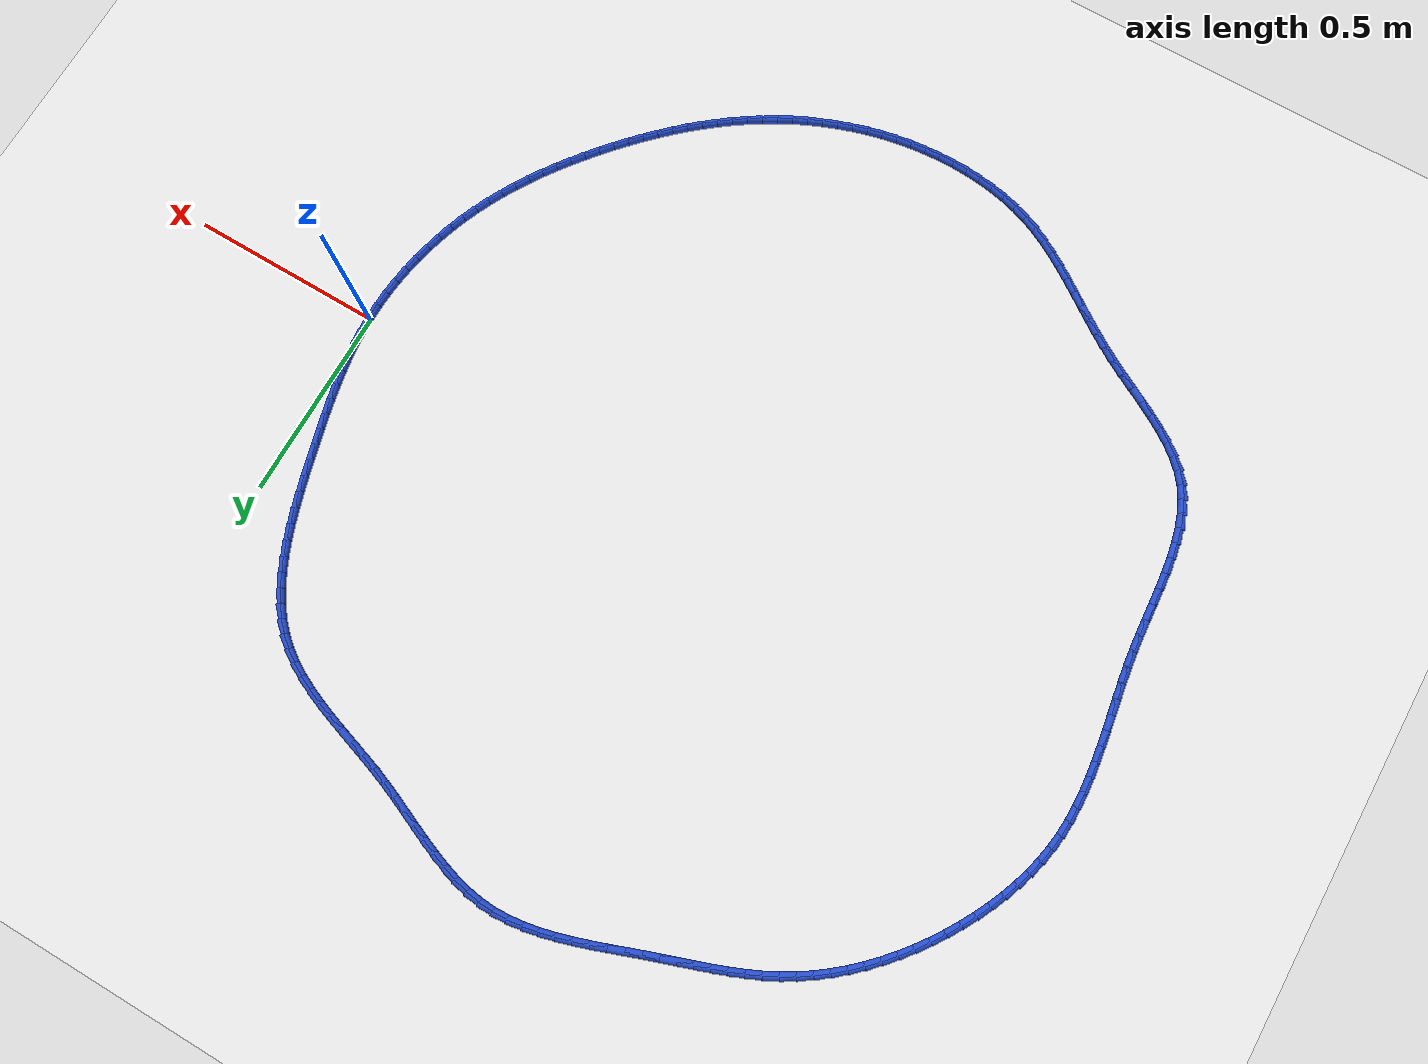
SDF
<sdf version="1.6">
 <world name="default">
  <light name="sun" type="directional">
   <pose>0 0 10 0 -0 0</pose>
   <diffuse>0.8 0.8 0.8 1</diffuse>
   <specular>0.2 0.2 0.2 1</specular>
   <attenuation>
    <range>1000</range>
    <constant>0.9</constant>
    <linear>0.01</linear>
    <quadratic>0.001</quadratic>
   </attenuation>
   <direction>-0.5 0.1 -0.9</direction>
  </light>
  <model name="ground_plane">
   <static>1</static>
   <link name="link">
    <collision name="collision">
     <geometry><plane><normal>0 0 1</normal><size>100 100</size></plane></geometry>
     <surface><friction><ode><mu>100</mu><mu2>50</mu2></ode></friction></surface>
    </collision>
    <visual name="visual">
     <cast_shadows>0</cast_shadows>
     <geometry><plane><normal>0 0 1</normal><size>100 100</size></plane></geometry>
     <material>
      <script><uri>file://media/materials/scripts/gazebo.material</uri><name>Gazebo/WhiteGlow</name></script>
     </material>
    </visual>
   </link>
  </model>
  <gravity>0 0 -9.8</gravity>
  <magnetic_field>6e-06 2.3e-05 -4.2e-05</magnetic_field>
  <atmosphere type="adiabatic"/>
  <physics name="default_physics" default="0" type="ode">
   <max_step_size>0.001</max_step_size>
   <real_time_factor>1</real_time_factor>
   <real_time_update_rate>1000</real_time_update_rate>
  </physics>
  <scene><ambient>0.4 0.4 0.4 1</ambient><background>0.7 0.7 0.7 1</background><shadows>1</shadows></scene>
  <spherical_coordinates>
   <surface_model>EARTH_WGS84</surface_model>
   <latitude_deg>0</latitude_deg>
   <longitude_deg>0</longitude_deg>
   <elevation>0</elevation>
   <heading_deg>0</heading_deg>
  </spherical_coordinates>
  <model name="line">
   <link name="link_0">
    <pose>2.2551405187698492e-17 -3.469446951953614e-17 0.01 0 1.57 -1.5224158664125622</pose>
    <collision name="collision">
     <geometry><cylinder><radius>0.01</radius><length>0.08</length></cylinder></geometry>
    </collision>
    <visual name="visual">
     <material>
      <script><name>Gazebo/Blue</name><uri>file://media/materials/scripts/gazebo.material</uri></script>
     </material>
     <geometry><cylinder><radius>0.01</radius><length>0.08</length></cylinder></geometry>
    </visual>
   </link>
   <link name="link_1">
    <pose>-0.0018524570608584854 0.0382594851531359 0.01 0 1.57 -1.4786715318647181</pose>
    <collision name="collision">
     <geometry><cylinder><radius>0.01</radius><length>0.08</length></cylinder></geometry>
    </collision>
    <visual name="visual">
     <material>
      <script><name>Gazebo/Blue</name><uri>file://media/materials/scripts/gazebo.material</uri></script>
     </material>
     <geometry><cylinder><radius>0.01</radius><length>0.08</length></cylinder></geometry>
    </visual>
   </link>
   <link name="link_2">
    <pose>-0.0053661504700810905 0.07629210786311716 0.01 0 1.57 -1.4393598620121903</pose>
    <collision name="collision">
     <geometry><cylinder><radius>0.01</radius><length>0.08</length></cylinder></geometry>
    </collision>
    <visual name="visual">
     <material>
      <script><name>Gazebo/Blue</name><uri>file://media/materials/scripts/gazebo.material</uri></script>
     </material>
     <geometry><cylinder><radius>0.01</radius><length>0.08</length></cylinder></geometry>
    </visual>
   </link>
   <link name="link_3">
    <pose>-0.010374809730890841 0.11417948986248341 0.01 0 1.57 -1.4047887472843967</pose>
    <collision name="collision">
     <geometry><cylinder><radius>0.01</radius><length>0.08</length></cylinder></geometry>
    </collision>
    <visual name="visual">
     <material>
      <script><name>Gazebo/Blue</name><uri>file://media/materials/scripts/gazebo.material</uri></script>
     </material>
     <geometry><cylinder><radius>0.01</radius><length>0.08</length></cylinder></geometry>
    </visual>
   </link>
   <link name="link_4">
    <pose>-0.016712164346510815 0.15200325288377434 0.01 0 1.57 -1.3751437921391525</pose>
    <collision name="collision">
     <geometry><cylinder><radius>0.01</radius><length>0.08</length></cylinder></geometry>
    </collision>
    <visual name="visual">
     <material>
      <script><name>Gazebo/Blue</name><uri>file://media/materials/scripts/gazebo.material</uri></script>
     </material>
     <geometry><cylinder><radius>0.01</radius><length>0.08</length></cylinder></geometry>
    </visual>
   </link>
   <link name="link_5">
    <pose>-0.024211943820164058 0.18984501865952952 0.01 0 1.57 -1.3505076286854965</pose>
    <collision name="collision">
     <geometry><cylinder><radius>0.01</radius><length>0.08</length></cylinder></geometry>
    </collision>
    <visual name="visual">
     <material>
      <script><name>Gazebo/Blue</name><uri>file://media/materials/scripts/gazebo.material</uri></script>
     </material>
     <geometry><cylinder><radius>0.01</radius><length>0.08</length></cylinder></geometry>
    </visual>
   </link>
   <link name="link_6">
    <pose>-0.0327078776550736 0.22778640892228855 0.01 0 1.57 -1.3308811730916426</pose>
    <collision name="collision">
     <geometry><cylinder><radius>0.01</radius><length>0.08</length></cylinder></geometry>
    </collision>
    <visual name="visual">
     <material>
      <script><name>Gazebo/Blue</name><uri>file://media/materials/scripts/gazebo.material</uri></script>
     </material>
     <geometry><cylinder><radius>0.01</radius><length>0.08</length></cylinder></geometry>
    </visual>
   </link>
   <link name="link_7">
    <pose>-0.04203369535446252 0.26590904540459104 0.01 0 1.57 -1.3162037856840971</pose>
    <collision name="collision">
     <geometry><cylinder><radius>0.01</radius><length>0.08</length></cylinder></geometry>
    </collision>
    <visual name="visual">
     <material>
      <script><name>Gazebo/Blue</name><uri>file://media/materials/scripts/gazebo.material</uri></script>
     </material>
     <geometry><cylinder><radius>0.01</radius><length>0.08</length></cylinder></geometry>
    </visual>
   </link>
   <link name="link_8">
    <pose>-0.05202312642155387 0.3042945498389767 0.01 0 1.57 -1.3063704763379724</pose>
    <collision name="collision">
     <geometry><cylinder><radius>0.01</radius><length>0.08</length></cylinder></geometry>
    </collision>
    <visual name="visual">
     <material>
      <script><name>Gazebo/Blue</name><uri>file://media/materials/scripts/gazebo.material</uri></script>
     </material>
     <geometry><cylinder><radius>0.01</radius><length>0.08</length></cylinder></geometry>
    </visual>
   </link>
   <link name="link_9">
    <pose>-0.0625099003595707 0.34302454395798515 0.01 0 1.57 -1.3009679392505522</pose>
    <collision name="collision">
     <geometry><cylinder><radius>0.01</radius><length>0.08</length></cylinder></geometry>
    </collision>
    <visual name="visual">
     <material>
      <script><name>Gazebo/Blue</name><uri>file://media/materials/scripts/gazebo.material</uri></script>
     </material>
     <geometry><cylinder><radius>0.01</radius><length>0.08</length></cylinder></geometry>
    </visual>
   </link>
   <link name="link_10">
    <pose>-0.0733368270392069 0.3821712123215931 0.01 0 1.57 -1.2944133006836243</pose>
    <collision name="collision">
     <geometry><cylinder><radius>0.01</radius><length>0.08</length></cylinder></geometry>
    </collision>
    <visual name="visual">
     <material>
      <script><name>Gazebo/Blue</name><uri>file://media/materials/scripts/gazebo.material</uri></script>
     </material>
     <geometry><cylinder><radius>0.01</radius><length>0.08</length></cylinder></geometry>
    </visual>
   </link>
   <link name="link_11">
    <pose>-0.08452622357509605 0.42162017866580087 0.01 0 1.57 -1.2816888618524753</pose>
    <collision name="collision">
     <geometry><cylinder><radius>0.01</radius><length>0.08</length></cylinder></geometry>
    </collision>
    <visual name="visual">
     <material>
      <script><name>Gazebo/Blue</name><uri>file://media/materials/scripts/gazebo.material</uri></script>
     </material>
     <geometry><cylinder><radius>0.01</radius><length>0.08</length></cylinder></geometry>
    </visual>
   </link>
   <link name="link_12">
    <pose>-0.09626498470366092 0.46108602217121886 0.01 0 1.57 -1.2624828384372422</pose>
    <collision name="collision">
     <geometry><cylinder><radius>0.01</radius><length>0.08</length></cylinder></geometry>
    </collision>
    <visual name="visual">
     <material>
      <script><name>Gazebo/Blue</name><uri>file://media/materials/scripts/gazebo.material</uri></script>
     </material>
     <geometry><cylinder><radius>0.01</radius><length>0.08</length></cylinder></geometry>
    </visual>
   </link>
   <link name="link_13">
    <pose>-0.10874609254493098 0.5002769954364393 0.01 0 1.57 -1.2364780944276674</pose>
    <collision name="collision">
     <geometry><cylinder><radius>0.01</radius><length>0.08</length></cylinder></geometry>
    </collision>
    <visual name="visual">
     <material>
      <script><name>Gazebo/Blue</name><uri>file://media/materials/scripts/gazebo.material</uri></script>
     </material>
     <geometry><cylinder><radius>0.01</radius><length>0.08</length></cylinder></geometry>
    </visual>
   </link>
   <link name="link_14">
    <pose>-0.12216252921893576 0.5389013510600548 0.01 0 1.57 -1.2031758468182105</pose>
    <collision name="collision">
     <geometry><cylinder><radius>0.01</radius><length>0.08</length></cylinder></geometry>
    </collision>
    <visual name="visual">
     <material>
      <script><name>Gazebo/Blue</name><uri>file://media/materials/scripts/gazebo.material</uri></script>
     </material>
     <geometry><cylinder><radius>0.01</radius><length>0.08</length></cylinder></geometry>
    </visual>
   </link>
   <link name="link_15">
    <pose>-0.13670727684570488 0.5766673416406576 0.01 0 1.57 -1.1619078081145913</pose>
    <collision name="collision">
     <geometry><cylinder><radius>0.01</radius><length>0.08</length></cylinder></geometry>
    </collision>
    <visual name="visual">
     <material>
      <script><name>Gazebo/Blue</name><uri>file://media/materials/scripts/gazebo.material</uri></script>
     </material>
     <geometry><cylinder><radius>0.01</radius><length>0.08</length></cylinder></geometry>
    </visual>
   </link>
   <link name="link_16">
    <pose>-0.15257331754526787 0.6132832197768407 0.01 0 1.57 -1.1118608027056225</pose>
    <collision name="collision">
     <geometry><cylinder><radius>0.01</radius><length>0.08</length></cylinder></geometry>
    </collision>
    <visual name="visual">
     <material>
      <script><name>Gazebo/Blue</name><uri>file://media/materials/scripts/gazebo.material</uri></script>
     </material>
     <geometry><cylinder><radius>0.01</radius><length>0.08</length></cylinder></geometry>
    </visual>
   </link>
   <link name="link_17">
    <pose>-0.16995363343765435 0.6484572380671964 0.01 0 1.57 -1.0521290007023256</pose>
    <collision name="collision">
     <geometry><cylinder><radius>0.01</radius><length>0.08</length></cylinder></geometry>
    </collision>
    <visual name="visual">
     <material>
      <script><name>Gazebo/Blue</name><uri>file://media/materials/scripts/gazebo.material</uri></script>
     </material>
     <geometry><cylinder><radius>0.01</radius><length>0.08</length></cylinder></geometry>
    </visual>
   </link>
   <link name="link_18">
    <pose>-0.1890412066428937 0.6818976491103167 0.01 0 1.57 -0.9818149807332603</pose>
    <collision name="collision">
     <geometry><cylinder><radius>0.01</radius><length>0.08</length></cylinder></geometry>
    </collision>
    <visual name="visual">
     <material>
      <script><name>Gazebo/Blue</name><uri>file://media/materials/scripts/gazebo.material</uri></script>
     </material>
     <geometry><cylinder><radius>0.01</radius><length>0.08</length></cylinder></geometry>
    </visual>
   </link>
   <link name="link_19">
    <pose>-0.21002901928101553 0.7133127055047943 0.01 0 1.57 -0.9002041779196223</pose>
    <collision name="collision">
     <geometry><cylinder><radius>0.01</radius><length>0.08</length></cylinder></geometry>
    </collision>
    <visual name="visual">
     <material>
      <script><name>Gazebo/Blue</name><uri>file://media/materials/scripts/gazebo.material</uri></script>
     </material>
     <geometry><cylinder><radius>0.01</radius><length>0.08</length></cylinder></geometry>
    </visual>
   </link>
   <link name="link_20">
    <pose>-0.23311005347204955 0.7424106598492223 0.01 0 1.57 -0.8070289224112783</pose>
    <collision name="collision">
     <geometry><cylinder><radius>0.01</radius><length>0.08</length></cylinder></geometry>
    </collision>
    <visual name="visual">
     <material>
      <script><name>Gazebo/Blue</name><uri>file://media/materials/scripts/gazebo.material</uri></script>
     </material>
     <geometry><cylinder><radius>0.01</radius><length>0.08</length></cylinder></geometry>
    </visual>
   </link>
   <link name="link_21">
    <pose>-0.25847729133602515 0.7688997647421925 0.01 0 1.57 -0.7033636517493684</pose>
    <collision name="collision">
     <geometry><cylinder><radius>0.01</radius><length>0.08</length></cylinder></geometry>
    </collision>
    <visual name="visual">
     <material>
      <script><name>Gazebo/Blue</name><uri>file://media/materials/scripts/gazebo.material</uri></script>
     </material>
     <geometry><cylinder><radius>0.01</radius><length>0.08</length></cylinder></geometry>
    </visual>
   </link>
   <link name="link_22">
    <pose>-0.286311918129234 0.7925050517288851 0.01 0 1.57 -0.6024252560384049</pose>
    <collision name="collision">
     <geometry><cylinder><radius>0.01</radius><length>0.08</length></cylinder></geometry>
    </collision>
    <visual name="visual">
     <material>
      <script><name>Gazebo/Blue</name><uri>file://media/materials/scripts/gazebo.material</uri></script>
     </material>
     <geometry><cylinder><radius>0.01</radius><length>0.08</length></cylinder></geometry>
    </visual>
   </link>
   <link name="link_23">
    <pose>-0.3165501497843575 0.8132999777739712 0.01 0 1.57 -0.5168796590764587</pose>
    <collision name="collision">
     <geometry><cylinder><radius>0.01</radius><length>0.08</length></cylinder></geometry>
    </collision>
    <visual name="visual">
     <material>
      <script><name>Gazebo/Blue</name><uri>file://media/materials/scripts/gazebo.material</uri></script>
     </material>
     <geometry><cylinder><radius>0.01</radius><length>0.08</length></cylinder></geometry>
    </visual>
   </link>
   <link name="link_24">
    <pose>-0.3488970390477859 0.8316867884796831 0.01 0 1.57 -0.44754463701837927</pose>
    <collision name="collision">
     <geometry><cylinder><radius>0.01</radius><length>0.08</length></cylinder></geometry>
    </collision>
    <visual name="visual">
     <material>
      <script><name>Gazebo/Blue</name><uri>file://media/materials/scripts/gazebo.material</uri></script>
     </material>
     <geometry><cylinder><radius>0.01</radius><length>0.08</length></cylinder></geometry>
    </visual>
   </link>
   <link name="link_25">
    <pose>-0.38304860594272677 0.8480805768950984 0.01 0 1.57 -0.39385267290261916</pose>
    <collision name="collision">
     <geometry><cylinder><radius>0.01</radius><length>0.08</length></cylinder></geometry>
    </collision>
    <visual name="visual">
     <material>
      <script><name>Gazebo/Blue</name><uri>file://media/materials/scripts/gazebo.material</uri></script>
     </material>
     <geometry><cylinder><radius>0.01</radius><length>0.08</length></cylinder></geometry>
    </visual>
   </link>
   <link name="link_26">
    <pose>-0.41870087049238797 0.8628964360692951 0.01 0 1.57 -0.35483097605906816</pose>
    <collision name="collision">
     <geometry><cylinder><radius>0.01</radius><length>0.08</length></cylinder></geometry>
    </collision>
    <visual name="visual">
     <material>
      <script><name>Gazebo/Blue</name><uri>file://media/materials/scripts/gazebo.material</uri></script>
     </material>
     <geometry><cylinder><radius>0.01</radius><length>0.08</length></cylinder></geometry>
    </visual>
   </link>
   <link name="link_27">
    <pose>-0.4555498527199769 0.8765494590513515 0.01 0 1.57 -0.3294735134559211</pose>
    <collision name="collision">
     <geometry><cylinder><radius>0.01</radius><length>0.08</length></cylinder></geometry>
    </collision>
    <visual name="visual">
     <material>
      <script><name>Gazebo/Blue</name><uri>file://media/materials/scripts/gazebo.material</uri></script>
     </material>
     <geometry><cylinder><radius>0.01</radius><length>0.08</length></cylinder></geometry>
    </visual>
   </link>
   <link name="link_28">
    <pose>-0.493291572648702 0.8894547388903461 0.01 0 1.57 -0.31694838914633827</pose>
    <collision name="collision">
     <geometry><cylinder><radius>0.01</radius><length>0.08</length></cylinder></geometry>
    </collision>
    <visual name="visual">
     <material>
      <script><name>Gazebo/Blue</name><uri>file://media/materials/scripts/gazebo.material</uri></script>
     </material>
     <geometry><cylinder><radius>0.01</radius><length>0.08</length></cylinder></geometry>
    </visual>
   </link>
   <link name="link_29">
    <pose>-0.5316220503017703 0.9020273686353564 0.01 0 1.57 -0.3166919745367716</pose>
    <collision name="collision">
     <geometry><cylinder><radius>0.01</radius><length>0.08</length></cylinder></geometry>
    </collision>
    <visual name="visual">
     <material>
      <script><name>Gazebo/Blue</name><uri>file://media/materials/scripts/gazebo.material</uri></script>
     </material>
     <geometry><cylinder><radius>0.01</radius><length>0.08</length></cylinder></geometry>
    </visual>
   </link>
   <link name="link_30">
    <pose>-0.5702373057023898 0.9146824413354606 0.01 0 1.57 -0.32843393407724975</pose>
    <collision name="collision">
     <geometry><cylinder><radius>0.01</radius><length>0.08</length></cylinder></geometry>
    </collision>
    <visual name="visual">
     <material>
      <script><name>Gazebo/Blue</name><uri>file://media/materials/scripts/gazebo.material</uri></script>
     </material>
     <geometry><cylinder><radius>0.01</radius><length>0.08</length></cylinder></geometry>
    </visual>
   </link>
   <link name="link_31">
    <pose>-0.6088333588737685 0.927835050039737 0.01 0 1.57 -0.35215004799600463</pose>
    <collision name="collision">
     <geometry><cylinder><radius>0.01</radius><length>0.08</length></cylinder></geometry>
    </collision>
    <visual name="visual">
     <material>
      <script><name>Gazebo/Blue</name><uri>file://media/materials/scripts/gazebo.material</uri></script>
     </material>
     <geometry><cylinder><radius>0.01</radius><length>0.08</length></cylinder></geometry>
    </visual>
   </link>
   <link name="link_32">
    <pose>-0.6471066775936392 0.9418992295531419 0.01 0 1.57 -0.38117288325636806</pose>
    <collision name="collision">
     <geometry><cylinder><radius>0.01</radius><length>0.08</length></cylinder></geometry>
    </collision>
    <visual name="visual">
     <material>
      <script><name>Gazebo/Blue</name><uri>file://media/materials/scripts/gazebo.material</uri></script>
     </material>
     <geometry><cylinder><radius>0.01</radius><length>0.08</length></cylinder></geometry>
    </visual>
   </link>
   <link name="link_33">
    <pose>-0.6848629285408614 0.9570309288578076 0.01 0 1.57 -0.39984912702733794</pose>
    <collision name="collision">
     <geometry><cylinder><radius>0.01</radius><length>0.08</length></cylinder></geometry>
    </collision>
    <visual name="visual">
     <material>
      <script><name>Gazebo/Blue</name><uri>file://media/materials/scripts/gazebo.material</uri></script>
     </material>
     <geometry><cylinder><radius>0.01</radius><length>0.08</length></cylinder></geometry>
    </visual>
   </link>
   <link name="link_34">
    <pose>-0.7221588296527172 0.9727927505749273 0.01 0 1.57 -0.4059308810750633</pose>
    <collision name="collision">
     <geometry><cylinder><radius>0.01</radius><length>0.08</length></cylinder></geometry>
    </collision>
    <visual name="visual">
     <material>
      <script><name>Gazebo/Blue</name><uri>file://media/materials/scripts/gazebo.material</uri></script>
     </material>
     <geometry><cylinder><radius>0.01</radius><length>0.08</length></cylinder></geometry>
    </visual>
   </link>
   <link name="link_35">
    <pose>-0.759086247323077 0.9886642258089833 0.01 0 1.57 -0.39918841952731327</pose>
    <collision name="collision">
     <geometry><cylinder><radius>0.01</radius><length>0.08</length></cylinder></geometry>
    </collision>
    <visual name="visual">
     <material>
      <script><name>Gazebo/Blue</name><uri>file://media/materials/scripts/gazebo.material</uri></script>
     </material>
     <geometry><cylinder><radius>0.01</radius><length>0.08</length></cylinder></geometry>
    </visual>
   </link>
   <link name="link_36">
    <pose>-0.7957370479458116 1.004124885664458 0.01 0 1.57 -0.3791571022842836</pose>
    <collision name="collision">
     <geometry><cylinder><radius>0.01</radius><length>0.08</length></cylinder></geometry>
    </collision>
    <visual name="visual">
     <material>
      <script><name>Gazebo/Blue</name><uri>file://media/materials/scripts/gazebo.material</uri></script>
     </material>
     <geometry><cylinder><radius>0.01</radius><length>0.08</length></cylinder></geometry>
    </visual>
   </link>
   <link name="link_37">
    <pose>-0.8322030979147917 1.0186542612458342 0.01 0 1.57 -0.3451486479870833</pose>
    <collision name="collision">
     <geometry><cylinder><radius>0.01</radius><length>0.08</length></cylinder></geometry>
    </collision>
    <visual name="visual">
     <material>
      <script><name>Gazebo/Blue</name><uri>file://media/materials/scripts/gazebo.material</uri></script>
     </material>
     <geometry><cylinder><radius>0.01</radius><length>0.08</length></cylinder></geometry>
    </visual>
   </link>
   <link name="link_38">
    <pose>-0.8685762636238878 1.0317318836575942 0.01 0 1.57 -0.29633679619192715</pose>
    <collision name="collision">
     <geometry><cylinder><radius>0.01</radius><length>0.08</length></cylinder></geometry>
    </collision>
    <visual name="visual">
     <material>
      <script><name>Gazebo/Blue</name><uri>file://media/materials/scripts/gazebo.material</uri></script>
     </material>
     <geometry><cylinder><radius>0.01</radius><length>0.08</length></cylinder></geometry>
    </visual>
   </link>
   <link name="link_39">
    <pose>-0.9049484114669711 1.04283728400422 0.01 0 1.57 -0.23195274142129868</pose>
    <collision name="collision">
     <geometry><cylinder><radius>0.01</radius><length>0.08</length></cylinder></geometry>
    </collision>
    <visual name="visual">
     <material>
      <script><name>Gazebo/Blue</name><uri>file://media/materials/scripts/gazebo.material</uri></script>
     </material>
     <geometry><cylinder><radius>0.01</radius><length>0.08</length></cylinder></geometry>
    </visual>
   </link>
   <link name="link_40">
    <pose>-0.941411407837912 1.051449993390195 0.01 0 1.57 -0.15162946516359266</pose>
    <collision name="collision">
     <geometry><cylinder><radius>0.01</radius><length>0.08</length></cylinder></geometry>
    </collision>
    <visual name="visual">
     <material>
      <script><name>Gazebo/Blue</name><uri>file://media/materials/scripts/gazebo.material</uri></script>
     </material>
     <geometry><cylinder><radius>0.01</radius><length>0.08</length></cylinder></geometry>
    </visual>
   </link>
   <link name="link_41">
    <pose>-0.9780571191305808 1.0570495429200006 0.01 0 1.57 -0.05655572588308514</pose>
    <collision name="collision">
     <geometry><cylinder><radius>0.01</radius><length>0.08</length></cylinder></geometry>
    </collision>
    <visual name="visual">
     <material>
      <script><name>Gazebo/Blue</name><uri>file://media/materials/scripts/gazebo.material</uri></script>
     </material>
     <geometry><cylinder><radius>0.01</radius><length>0.08</length></cylinder></geometry>
    </visual>
   </link>
   <link name="link_42">
    <pose>-1.0149739178853434 1.0591396281603196 0.01 0 1.57 0.038547909194739195</pose>
    <collision name="collision">
     <geometry><cylinder><radius>0.01</radius><length>0.08</length></cylinder></geometry>
    </collision>
    <visual name="visual">
     <material>
      <script><name>Gazebo/Blue</name><uri>file://media/materials/scripts/gazebo.material</uri></script>
     </material>
     <geometry><cylinder><radius>0.01</radius><length>0.08</length></cylinder></geometry>
    </visual>
   </link>
   <link name="link_43">
    <pose>-1.0521806695792402 1.0577046748520433 0.01 0 1.57 0.12045471205789136</pose>
    <collision name="collision">
     <geometry><cylinder><radius>0.01</radius><length>0.08</length></cylinder></geometry>
    </collision>
    <visual name="visual">
     <material>
      <script><name>Gazebo/Blue</name><uri>file://media/materials/scripts/gazebo.material</uri></script>
     </material>
     <geometry><cylinder><radius>0.01</radius><length>0.08</length></cylinder></geometry>
    </visual>
   </link>
   <link name="link_44">
    <pose>-1.089632274921135 1.0531715068561736 0.01 0 1.57 0.18865319458546626</pose>
    <collision name="collision">
     <geometry><cylinder><radius>0.01</radius><length>0.08</length></cylinder></geometry>
    </collision>
    <visual name="visual">
     <material>
      <script><name>Gazebo/Blue</name><uri>file://media/materials/scripts/gazebo.material</uri></script>
     </material>
     <geometry><cylinder><radius>0.01</radius><length>0.08</length></cylinder></geometry>
    </visual>
   </link>
   <link name="link_45">
    <pose>-1.1272812516252952 1.0459834294868626 0.01 0 1.57 0.2437324239380083</pose>
    <collision name="collision">
     <geometry><cylinder><radius>0.01</radius><length>0.08</length></cylinder></geometry>
    </collision>
    <visual name="visual">
     <material>
      <script><name>Gazebo/Blue</name><uri>file://media/materials/scripts/gazebo.material</uri></script>
     </material>
     <geometry><cylinder><radius>0.01</radius><length>0.08</length></cylinder></geometry>
    </visual>
   </link>
   <link name="link_46">
    <pose>-1.1650801174059864 1.0365837480582631 0.01 0 1.57 0.2865503266886196</pose>
    <collision name="collision">
     <geometry><cylinder><radius>0.01</radius><length>0.08</length></cylinder></geometry>
    </collision>
    <visual name="visual">
     <material>
      <script><name>Gazebo/Blue</name><uri>file://media/materials/scripts/gazebo.material</uri></script>
     </material>
     <geometry><cylinder><radius>0.01</radius><length>0.08</length></cylinder></geometry>
    </visual>
   </link>
   <link name="link_47">
    <pose>-1.202981389977476 1.025415767884527 0.01 0 1.57 0.3179735040459937</pose>
    <collision name="collision">
     <geometry><cylinder><radius>0.01</radius><length>0.08</length></cylinder></geometry>
    </collision>
    <visual name="visual">
     <material>
      <script><name>Gazebo/Blue</name><uri>file://media/materials/scripts/gazebo.material</uri></script>
     </material>
     <geometry><cylinder><radius>0.01</radius><length>0.08</length></cylinder></geometry>
    </visual>
   </link>
   <link name="link_48">
    <pose>-1.2409375870540298 1.012922794279807 0.01 0 1.57 0.3387240236345106</pose>
    <collision name="collision">
     <geometry><cylinder><radius>0.01</radius><length>0.08</length></cylinder></geometry>
    </collision>
    <visual name="visual">
     <material>
      <script><name>Gazebo/Blue</name><uri>file://media/materials/scripts/gazebo.material</uri></script>
     </material>
     <geometry><cylinder><radius>0.01</radius><length>0.08</length></cylinder></geometry>
    </visual>
   </link>
   <link name="link_49">
    <pose>-1.278901226349915 0.9995481325582553 0.01 0 1.57 0.3492982826263346</pose>
    <collision name="collision">
     <geometry><cylinder><radius>0.01</radius><length>0.08</length></cylinder></geometry>
    </collision>
    <visual name="visual">
     <material>
      <script><name>Gazebo/Blue</name><uri>file://media/materials/scripts/gazebo.material</uri></script>
     </material>
     <geometry><cylinder><radius>0.01</radius><length>0.08</length></cylinder></geometry>
    </visual>
   </link>
   <link name="link_50">
    <pose>-1.316824825579399 0.9857350880340245 0.01 0 1.57 0.34992713526503894</pose>
    <collision name="collision">
     <geometry><cylinder><radius>0.01</radius><length>0.08</length></cylinder></geometry>
    </collision>
    <visual name="visual">
     <material>
      <script><name>Gazebo/Blue</name><uri>file://media/materials/scripts/gazebo.material</uri></script>
     </material>
     <geometry><cylinder><radius>0.01</radius><length>0.08</length></cylinder></geometry>
    </visual>
   </link>
   <link name="link_51">
    <pose>-1.3546609024567469 0.9719269660212666 0.01 0 1.57 0.3413518966211679</pose>
    <collision name="collision">
     <geometry><cylinder><radius>0.01</radius><length>0.08</length></cylinder></geometry>
    </collision>
    <visual name="visual">
     <material>
      <script><name>Gazebo/Blue</name><uri>file://media/materials/scripts/gazebo.material</uri></script>
     </material>
     <geometry><cylinder><radius>0.01</radius><length>0.08</length></cylinder></geometry>
    </visual>
   </link>
   <link name="link_52">
    <pose>-1.3923595646980726 0.9585341895688773 0.01 0 1.57 0.3337961311876104</pose>
    <collision name="collision">
     <geometry><cylinder><radius>0.01</radius><length>0.08</length></cylinder></geometry>
    </collision>
    <visual name="visual">
     <material>
      <script><name>Gazebo/Blue</name><uri>file://media/materials/scripts/gazebo.material</uri></script>
     </material>
     <geometry><cylinder><radius>0.01</radius><length>0.08</length></cylinder></geometry>
    </visual>
   </link>
   <link name="link_53">
    <pose>-1.4298394082886512 0.945537232395361 0.01 0 1.57 0.33469289615882825</pose>
    <collision name="collision">
     <geometry><cylinder><radius>0.01</radius><length>0.08</length></cylinder></geometry>
    </collision>
    <visual name="visual">
     <material>
      <script><name>Gazebo/Blue</name><uri>file://media/materials/scripts/gazebo.material</uri></script>
     </material>
     <geometry><cylinder><radius>0.01</radius><length>0.08</length></cylinder></geometry>
    </visual>
   </link>
   <link name="link_54">
    <pose>-1.4669969059159087 0.9326147156442594 0.01 0 1.57 0.3444100366077265</pose>
    <collision name="collision">
     <geometry><cylinder><radius>0.01</radius><length>0.08</length></cylinder></geometry>
    </collision>
    <visual name="visual">
     <material>
      <script><name>Gazebo/Blue</name><uri>file://media/materials/scripts/gazebo.material</uri></script>
     </material>
     <geometry><cylinder><radius>0.01</radius><length>0.08</length></cylinder></geometry>
    </visual>
   </link>
   <link name="link_55">
    <pose>-1.503728071916829 0.9194390066780236 0.01 0 1.57 0.3631521105262741</pose>
    <collision name="collision">
     <geometry><cylinder><radius>0.01</radius><length>0.08</length></cylinder></geometry>
    </collision>
    <visual name="visual">
     <material>
      <script><name>Gazebo/Blue</name><uri>file://media/materials/scripts/gazebo.material</uri></script>
     </material>
     <geometry><cylinder><radius>0.01</radius><length>0.08</length></cylinder></geometry>
    </visual>
   </link>
   <link name="link_56">
    <pose>-1.539928920628394 0.9056824728591054 0.01 0 1.57 0.39108638559215697</pose>
    <collision name="collision">
     <geometry><cylinder><radius>0.01</radius><length>0.08</length></cylinder></geometry>
    </collision>
    <visual name="visual">
     <material>
      <script><name>Gazebo/Blue</name><uri>file://media/materials/scripts/gazebo.material</uri></script>
     </material>
     <geometry><cylinder><radius>0.01</radius><length>0.08</length></cylinder></geometry>
    </visual>
   </link>
   <link name="link_57">
    <pose>-1.5754954663875878 0.8910174815499556 0.01 0 1.57 0.4282932569173917</pose>
    <collision name="collision">
     <geometry><cylinder><radius>0.01</radius><length>0.08</length></cylinder></geometry>
    </collision>
    <visual name="visual">
     <material>
      <script><name>Gazebo/Blue</name><uri>file://media/materials/scripts/gazebo.material</uri></script>
     </material>
     <geometry><cylinder><radius>0.01</radius><length>0.08</length></cylinder></geometry>
    </visual>
   </link>
   <link name="link_58">
    <pose>-1.6103237235313934 0.8751164001130258 0.01 0 1.57 0.4746918838837033</pose>
    <collision name="collision">
     <geometry><cylinder><radius>0.01</radius><length>0.08</length></cylinder></geometry>
    </collision>
    <visual name="visual">
     <material>
      <script><name>Gazebo/Blue</name><uri>file://media/materials/scripts/gazebo.material</uri></script>
     </material>
     <geometry><cylinder><radius>0.01</radius><length>0.08</length></cylinder></geometry>
    </visual>
   </link>
   <link name="link_59">
    <pose>-1.6443097063967929 0.857651595910767 0.01 0 1.57 0.5295334350832208</pose>
    <collision name="collision">
     <geometry><cylinder><radius>0.01</radius><length>0.08</length></cylinder></geometry>
    </collision>
    <visual name="visual">
     <material>
      <script><name>Gazebo/Blue</name><uri>file://media/materials/scripts/gazebo.material</uri></script>
     </material>
     <geometry><cylinder><radius>0.01</radius><length>0.08</length></cylinder></geometry>
    </visual>
   </link>
   <link name="link_60">
    <pose>-1.6773519302405382 0.838312297921994 0.01 0 1.57 0.5864700486711794</pose>
    <collision name="collision">
     <geometry><cylinder><radius>0.01</radius><length>0.08</length></cylinder></geometry>
    </collision>
    <visual name="visual">
     <material>
      <script><name>Gazebo/Blue</name><uri>file://media/materials/scripts/gazebo.material</uri></script>
     </material>
     <geometry><cylinder><radius>0.01</radius><length>0.08</length></cylinder></geometry>
    </visual>
   </link>
   <link name="link_61">
    <pose>-1.709384554360176 0.8170280531673858 0.01 0 1.57 0.6410754966665696</pose>
    <collision name="collision">
     <geometry><cylinder><radius>0.01</radius><length>0.08</length></cylinder></geometry>
    </collision>
    <visual name="visual">
     <material>
      <script><name>Gazebo/Blue</name><uri>file://media/materials/scripts/gazebo.material</uri></script>
     </material>
     <geometry><cylinder><radius>0.01</radius><length>0.08</length></cylinder></geometry>
    </visual>
   </link>
   <link name="link_62">
    <pose>-1.7403682954845774 0.7939074632795774 0.01 0 1.57 0.693365747215571</pose>
    <collision name="collision">
     <geometry><cylinder><radius>0.01</radius><length>0.08</length></cylinder></geometry>
    </collision>
    <visual name="visual">
     <material>
      <script><name>Gazebo/Blue</name><uri>file://media/materials/scripts/gazebo.material</uri></script>
     </material>
     <geometry><cylinder><radius>0.01</radius><length>0.08</length></cylinder></geometry>
    </visual>
   </link>
   <link name="link_63">
    <pose>-1.7702645044642762 0.7690634052447409 0.01 0 1.57 0.7434961846682222</pose>
    <collision name="collision">
     <geometry><cylinder><radius>0.01</radius><length>0.08</length></cylinder></geometry>
    </collision>
    <visual name="visual">
     <material>
      <script><name>Gazebo/Blue</name><uri>file://media/materials/scripts/gazebo.material</uri></script>
     </material>
     <geometry><cylinder><radius>0.01</radius><length>0.08</length></cylinder></geometry>
    </visual>
   </link>
   <link name="link_64">
    <pose>-1.7990345321498051 0.74260875604905 0.01 0 1.57 0.7916468468557558</pose>
    <collision name="collision">
     <geometry><cylinder><radius>0.01</radius><length>0.08</length></cylinder></geometry>
    </collision>
    <visual name="visual">
     <material>
      <script><name>Gazebo/Blue</name><uri>file://media/materials/scripts/gazebo.material</uri></script>
     </material>
     <geometry><cylinder><radius>0.01</radius><length>0.08</length></cylinder></geometry>
    </visual>
   </link>
   <link name="link_65">
    <pose>-1.8266397293916967 0.7146563926786768 0.01 0 1.57 0.8380144245530833</pose>
    <collision name="collision">
     <geometry><cylinder><radius>0.01</radius><length>0.08</length></cylinder></geometry>
    </collision>
    <visual name="visual">
     <material>
      <script><name>Gazebo/Blue</name><uri>file://media/materials/scripts/gazebo.material</uri></script>
     </material>
     <geometry><cylinder><radius>0.01</radius><length>0.08</length></cylinder></geometry>
    </visual>
   </link>
   <link name="link_66">
    <pose>-1.8530414470404848 0.6853191921197941 0.01 0 1.57 0.8828062135947151</pose>
    <collision name="collision">
     <geometry><cylinder><radius>0.01</radius><length>0.08</length></cylinder></geometry>
    </collision>
    <visual name="visual">
     <material>
      <script><name>Gazebo/Blue</name><uri>file://media/materials/scripts/gazebo.material</uri></script>
     </material>
     <geometry><cylinder><radius>0.01</radius><length>0.08</length></cylinder></geometry>
    </visual>
   </link>
   <link name="link_67">
    <pose>-1.8782010359467025 0.6547100313585756 0.01 0 1.57 0.9262358215345126</pose>
    <collision name="collision">
     <geometry><cylinder><radius>0.01</radius><length>0.08</length></cylinder></geometry>
    </collision>
    <visual name="visual">
     <material>
      <script><name>Gazebo/Blue</name><uri>file://media/materials/scripts/gazebo.material</uri></script>
     </material>
     <geometry><cylinder><radius>0.01</radius><length>0.08</length></cylinder></geometry>
    </visual>
   </link>
   <link name="link_68">
    <pose>-1.9020798469608835 0.6229417873811934 0.01 0 1.57 0.968520373437604</pose>
    <collision name="collision">
     <geometry><cylinder><radius>0.01</radius><length>0.08</length></cylinder></geometry>
    </collision>
    <visual name="visual">
     <material>
      <script><name>Gazebo/Blue</name><uri>file://media/materials/scripts/gazebo.material</uri></script>
     </material>
     <geometry><cylinder><radius>0.01</radius><length>0.08</length></cylinder></geometry>
    </visual>
   </link>
   <link name="link_69">
    <pose>-1.9246392309335598 0.5901273371738209 0.01 0 1.57 1.009878954382426</pose>
    <collision name="collision">
     <geometry><cylinder><radius>0.01</radius><length>0.08</length></cylinder></geometry>
    </collision>
    <visual name="visual">
     <material>
      <script><name>Gazebo/Blue</name><uri>file://media/materials/scripts/gazebo.material</uri></script>
     </material>
     <geometry><cylinder><radius>0.01</radius><length>0.08</length></cylinder></geometry>
    </visual>
   </link>
   <link name="link_70">
    <pose>-1.9458405387152649 0.5563795577226305 0.01 0 1.57 1.0507747737547097</pose>
    <collision name="collision">
     <geometry><cylinder><radius>0.01</radius><length>0.08</length></cylinder></geometry>
    </collision>
    <visual name="visual">
     <material>
      <script><name>Gazebo/Blue</name><uri>file://media/materials/scripts/gazebo.material</uri></script>
     </material>
     <geometry><cylinder><radius>0.01</radius><length>0.08</length></cylinder></geometry>
    </visual>
   </link>
   <link name="link_71">
    <pose>-1.9656343075133342 0.5218107506079419 0.01 0 1.57 1.0933238342998646</pose>
    <collision name="collision">
     <geometry><cylinder><radius>0.01</radius><length>0.08</length></cylinder></geometry>
    </collision>
    <visual name="visual">
     <material>
      <script><name>Gazebo/Blue</name><uri>file://media/materials/scripts/gazebo.material</uri></script>
     </material>
     <geometry><cylinder><radius>0.01</radius><length>0.08</length></cylinder></geometry>
    </visual>
   </link>
   <link name="link_72">
    <pose>-1.9838892445343146 0.4865288631456937 0.01 0 1.57 1.1387741753433998</pose>
    <collision name="collision">
     <geometry><cylinder><radius>0.01</radius><length>0.08</length></cylinder></geometry>
    </collision>
    <visual name="visual">
     <material>
      <script><name>Gazebo/Blue</name><uri>file://media/materials/scripts/gazebo.material</uri></script>
     </material>
     <geometry><cylinder><radius>0.01</radius><length>0.08</length></cylinder></geometry>
    </visual>
   </link>
   <link name="link_73">
    <pose>-2.0004366194129575 0.45063985055743583 0.01 0 1.57 1.1875730688106443</pose>
    <collision name="collision">
     <geometry><cylinder><radius>0.01</radius><length>0.08</length></cylinder></geometry>
    </collision>
    <visual name="visual">
     <material>
      <script><name>Gazebo/Blue</name><uri>file://media/materials/scripts/gazebo.material</uri></script>
     </material>
     <geometry><cylinder><radius>0.01</radius><length>0.08</length></cylinder></geometry>
    </visual>
   </link>
   <link name="link_74">
    <pose>-2.015107508253352 0.4142496577667377 0.01 0 1.57 1.2401747007690214</pose>
    <collision name="collision">
     <geometry><cylinder><radius>0.01</radius><length>0.08</length></cylinder></geometry>
    </collision>
    <visual name="visual">
     <material>
      <script><name>Gazebo/Blue</name><uri>file://media/materials/scripts/gazebo.material</uri></script>
     </material>
     <geometry><cylinder><radius>0.01</radius><length>0.08</length></cylinder></geometry>
    </visual>
   </link>
   <link name="link_75">
    <pose>-2.0277329871595873 0.37746422969717036 0.01 0 1.57 1.2970318339333344</pose>
    <collision name="collision">
     <geometry><cylinder><radius>0.01</radius><length>0.08</length></cylinder></geometry>
    </collision>
    <visual name="visual">
     <material>
      <script><name>Gazebo/Blue</name><uri>file://media/materials/scripts/gazebo.material</uri></script>
     </material>
     <geometry><cylinder><radius>0.01</radius><length>0.08</length></cylinder></geometry>
    </visual>
   </link>
   <link name="link_76">
    <pose>-2.038144132235754 0.3403895112723036 0.01 0 1.57 1.3585737376439848</pose>
    <collision name="collision">
     <geometry><cylinder><radius>0.01</radius><length>0.08</length></cylinder></geometry>
    </collision>
    <visual name="visual">
     <material>
      <script><name>Gazebo/Blue</name><uri>file://media/materials/scripts/gazebo.material</uri></script>
     </material>
     <geometry><cylinder><radius>0.01</radius><length>0.08</length></cylinder></geometry>
    </visual>
   </link>
   <link name="link_77">
    <pose>-2.046172019585941 0.3031314474157074 0.01 0 1.57 1.4245852767962004</pose>
    <collision name="collision">
     <geometry><cylinder><radius>0.01</radius><length>0.08</length></cylinder></geometry>
    </collision>
    <visual name="visual">
     <material>
      <script><name>Gazebo/Blue</name><uri>file://media/materials/scripts/gazebo.material</uri></script>
     </material>
     <geometry><cylinder><radius>0.01</radius><length>0.08</length></cylinder></geometry>
    </visual>
   </link>
   <link name="link_78">
    <pose>-2.05167121678409 0.2657884794263393 0.01 0 1.57 1.4884284950947293</pose>
    <collision name="collision">
     <geometry><cylinder><radius>0.01</radius><length>0.08</length></cylinder></geometry>
    </collision>
    <visual name="visual">
     <material>
      <script><name>Gazebo/Blue</name><uri>file://media/materials/scripts/gazebo.material</uri></script>
     </material>
     <geometry><cylinder><radius>0.01</radius><length>0.08</length></cylinder></geometry>
    </visual>
   </link>
   <link name="link_79">
    <pose>-2.054759884293083 0.22837485199468757 0.01 0 1.57 1.5451654917937003</pose>
    <collision name="collision">
     <geometry><cylinder><radius>0.01</radius><length>0.08</length></cylinder></geometry>
    </collision>
    <visual name="visual">
     <material>
      <script><name>Gazebo/Blue</name><uri>file://media/materials/scripts/gazebo.material</uri></script>
     </material>
     <geometry><cylinder><radius>0.01</radius><length>0.08</length></cylinder></geometry>
    </visual>
   </link>
   <link name="link_80">
    <pose>-2.0557218396508423 0.19085189577420814 0.01 0 1.57 -1.5474841677003817</pose>
    <collision name="collision">
     <geometry><cylinder><radius>0.01</radius><length>0.08</length></cylinder></geometry>
    </collision>
    <visual name="visual">
     <material>
      <script><name>Gazebo/Blue</name><uri>file://media/materials/scripts/gazebo.material</uri></script>
     </material>
     <geometry><cylinder><radius>0.01</radius><length>0.08</length></cylinder></geometry>
    </visual>
   </link>
   <link name="link_81">
    <pose>-2.054843470110274 0.15318012060225936 0.01 0 1.57 -1.5066398636417966</pose>
    <collision name="collision">
     <geometry><cylinder><radius>0.01</radius><length>0.08</length></cylinder></geometry>
    </collision>
    <visual name="visual">
     <material>
      <script><name>Gazebo/Blue</name><uri>file://media/materials/scripts/gazebo.material</uri></script>
     </material>
     <geometry><cylinder><radius>0.01</radius><length>0.08</length></cylinder></geometry>
    </visual>
   </link>
   <link name="link_82">
    <pose>-2.0524111629242845 0.11532003631619978 0.01 0 1.57 -1.4739601371621038</pose>
    <collision name="collision">
     <geometry><cylinder><radius>0.01</radius><length>0.08</length></cylinder></geometry>
    </collision>
    <visual name="visual">
     <material>
      <script><name>Gazebo/Blue</name><uri>file://media/materials/scripts/gazebo.material</uri></script>
     </material>
     <geometry><cylinder><radius>0.01</radius><length>0.08</length></cylinder></geometry>
    </visual>
   </link>
   <link name="link_83">
    <pose>-2.048711305345778 0.07723215275338867 0.01 0 1.57 -1.4493528554021393</pose>
    <collision name="collision">
     <geometry><cylinder><radius>0.01</radius><length>0.08</length></cylinder></geometry>
    </collision>
    <visual name="visual">
     <material>
      <script><name>Gazebo/Blue</name><uri>file://media/materials/scripts/gazebo.material</uri></script>
     </material>
     <geometry><cylinder><radius>0.01</radius><length>0.08</length></cylinder></geometry>
    </visual>
   </link>
   <link name="link_84">
    <pose>-2.0440302846276612 0.03887697975118409 0.01 0 1.57 -1.4326359975624114</pose>
    <collision name="collision">
     <geometry><cylinder><radius>0.01</radius><length>0.08</length></cylinder></geometry>
    </collision>
    <visual name="visual">
     <material>
      <script><name>Gazebo/Blue</name><uri>file://media/materials/scripts/gazebo.material</uri></script>
     </material>
     <geometry><cylinder><radius>0.01</radius><length>0.08</length></cylinder></geometry>
    </visual>
   </link>
   <link name="link_85">
    <pose>-2.038654488022839 0.00021502714694554212 0.01 0 1.57 -1.423587799224604</pose>
    <collision name="collision">
     <geometry><cylinder><radius>0.01</radius><length>0.08</length></cylinder></geometry>
    </collision>
    <visual name="visual">
     <material>
      <script><name>Gazebo/Blue</name><uri>file://media/materials/scripts/gazebo.material</uri></script>
     </material>
     <geometry><cylinder><radius>0.01</radius><length>0.08</length></cylinder></geometry>
    </visual>
   </link>
   <link name="link_86">
    <pose>-2.032870302784218 -0.03879319522196866 0.01 0 1.57 -1.4219786416331668</pose>
    <collision name="collision">
     <geometry><cylinder><radius>0.01</radius><length>0.08</length></cylinder></geometry>
    </collision>
    <visual name="visual">
     <material>
      <script><name>Gazebo/Blue</name><uri>file://media/materials/scripts/gazebo.material</uri></script>
     </material>
     <geometry><cylinder><radius>0.01</radius><length>0.08</length></cylinder></geometry>
    </visual>
   </link>
   <link name="link_87">
    <pose>-2.026964116164702 -0.07818717751819974 0.01 0 1.57 -1.4275867816083252</pose>
    <collision name="collision">
     <geometry><cylinder><radius>0.01</radius><length>0.08</length></cylinder></geometry>
    </collision>
    <visual name="visual">
     <material>
      <script><name>Gazebo/Blue</name><uri>file://media/materials/scripts/gazebo.material</uri></script>
     </material>
     <geometry><cylinder><radius>0.01</radius><length>0.08</length></cylinder></geometry>
    </visual>
   </link>
   <link name="link_88">
    <pose>-2.0212223154171975 -0.11800640990438906 0.01 0 1.57 -1.4402006304692334</pose>
    <collision name="collision">
     <geometry><cylinder><radius>0.01</radius><length>0.08</length></cylinder></geometry>
    </collision>
    <visual name="visual">
     <material>
      <script><name>Gazebo/Blue</name><uri>file://media/materials/scripts/gazebo.material</uri></script>
     </material>
     <geometry><cylinder><radius>0.01</radius><length>0.08</length></cylinder></geometry>
    </visual>
   </link>
   <link name="link_89">
    <pose>-2.0159312877946105 -0.1582903825431786 0.01 0 1.57 -1.4596101042756437</pose>
    <collision name="collision">
     <geometry><cylinder><radius>0.01</radius><length>0.08</length></cylinder></geometry>
    </collision>
    <visual name="visual">
     <material>
      <script><name>Gazebo/Blue</name><uri>file://media/materials/scripts/gazebo.material</uri></script>
     </material>
     <geometry><cylinder><radius>0.01</radius><length>0.08</length></cylinder></geometry>
    </visual>
   </link>
   <link name="link_90">
    <pose>-2.011377420549846 -0.19907858559720806 0.01 0 1.57 -1.4841811122790962</pose>
    <collision name="collision">
     <geometry><cylinder><radius>0.01</radius><length>0.08</length></cylinder></geometry>
    </collision>
    <visual name="visual">
     <material>
      <script><name>Gazebo/Blue</name><uri>file://media/materials/scripts/gazebo.material</uri></script>
     </material>
     <geometry><cylinder><radius>0.01</radius><length>0.08</length></cylinder></geometry>
    </visual>
   </link>
   <link name="link_91">
    <pose>-2.007790644908977 -0.24038543460381878 0.01 0 1.57 -1.5022552976345653</pose>
    <collision name="collision">
     <geometry><cylinder><radius>0.01</radius><length>0.08</length></cylinder></geometry>
    </collision>
    <visual name="visual">
     <material>
      <script><name>Gazebo/Blue</name><uri>file://media/materials/scripts/gazebo.material</uri></script>
     </material>
     <geometry><cylinder><radius>0.01</radius><length>0.08</length></cylinder></geometry>
    </visual>
   </link>
   <link name="link_92">
    <pose>-2.004932671149639 -0.28201738741188637 0.01 0 1.57 -1.508490369314446</pose>
    <collision name="collision">
     <geometry><cylinder><radius>0.01</radius><length>0.08</length></cylinder></geometry>
    </collision>
    <visual name="visual">
     <material>
      <script><name>Gazebo/Blue</name><uri>file://media/materials/scripts/gazebo.material</uri></script>
     </material>
     <geometry><cylinder><radius>0.01</radius><length>0.08</length></cylinder></geometry>
    </visual>
   </link>
   <link name="link_93">
    <pose>-2.002333600575328 -0.32367803405317774 0.01 0 1.57 -1.5029719027319648</pose>
    <collision name="collision">
     <geometry><cylinder><radius>0.01</radius><length>0.08</length></cylinder></geometry>
    </collision>
    <visual name="visual">
     <material>
      <script><name>Gazebo/Blue</name><uri>file://media/materials/scripts/gazebo.material</uri></script>
     </material>
     <geometry><cylinder><radius>0.01</radius><length>0.08</length></cylinder></geometry>
    </visual>
   </link>
   <link name="link_94">
    <pose>-1.9995218858064148 -0.365070232306168 0.01 0 1.57 -1.4853765543723403</pose>
    <collision name="collision">
     <geometry><cylinder><radius>0.01</radius><length>0.08</length></cylinder></geometry>
    </collision>
    <visual name="visual">
     <material>
      <script><name>Gazebo/Blue</name><uri>file://media/materials/scripts/gazebo.material</uri></script>
     </material>
     <geometry><cylinder><radius>0.01</radius><length>0.08</length></cylinder></geometry>
    </visual>
   </link>
   <link name="link_95">
    <pose>-1.9960259794632704 -0.40589683994932957 0.01 0 1.57 -1.4549214903388552</pose>
    <collision name="collision">
     <geometry><cylinder><radius>0.01</radius><length>0.08</length></cylinder></geometry>
    </collision>
    <visual name="visual">
     <material>
      <script><name>Gazebo/Blue</name><uri>file://media/materials/scripts/gazebo.material</uri></script>
     </material>
     <geometry><cylinder><radius>0.01</radius><length>0.08</length></cylinder></geometry>
    </visual>
   </link>
   <link name="link_96">
    <pose>-1.9913743341662686 -0.4458607147611379 0.01 0 1.57 -1.4103753269256878</pose>
    <collision name="collision">
     <geometry><cylinder><radius>0.01</radius><length>0.08</length></cylinder></geometry>
    </collision>
    <visual name="visual">
     <material>
      <script><name>Gazebo/Blue</name><uri>file://media/materials/scripts/gazebo.material</uri></script>
     </material>
     <geometry><cylinder><radius>0.01</radius><length>0.08</length></cylinder></geometry>
    </visual>
   </link>
   <link name="link_97">
    <pose>-1.9850954025357794 -0.48466471452006715 0.01 0 1.57 -1.3501269121032808</pose>
    <collision name="collision">
     <geometry><cylinder><radius>0.01</radius><length>0.08</length></cylinder></geometry>
    </collision>
    <visual name="visual">
     <material>
      <script><name>Gazebo/Blue</name><uri>file://media/materials/scripts/gazebo.material</uri></script>
     </material>
     <geometry><cylinder><radius>0.01</radius><length>0.08</length></cylinder></geometry>
    </visual>
   </link>
   <link name="link_98">
    <pose>-1.9767176371921755 -0.5220116970045916 0.01 0 1.57 -1.2723870069478223</pose>
    <collision name="collision">
     <geometry><cylinder><radius>0.01</radius><length>0.08</length></cylinder></geometry>
    </collision>
    <visual name="visual">
     <material>
      <script><name>Gazebo/Blue</name><uri>file://media/materials/scripts/gazebo.material</uri></script>
     </material>
     <geometry><cylinder><radius>0.01</radius><length>0.08</length></cylinder></geometry>
    </visual>
   </link>
   <link name="link_99">
    <pose>-1.9657694907558287 -0.557604519993186 0.01 0 1.57 -1.1756384105161668</pose>
    <collision name="collision">
     <geometry><cylinder><radius>0.01</radius><length>0.08</length></cylinder></geometry>
    </collision>
    <visual name="visual">
     <material>
      <script><name>Gazebo/Blue</name><uri>file://media/materials/scripts/gazebo.material</uri></script>
     </material>
     <geometry><cylinder><radius>0.01</radius><length>0.08</length></cylinder></geometry>
    </visual>
   </link>
   <link name="link_100">
    <pose>-1.9517794158471113 -0.5911460412643239 0.01 0 1.57 -1.0594438168292521</pose>
    <collision name="collision">
     <geometry><cylinder><radius>0.01</radius><length>0.08</length></cylinder></geometry>
    </collision>
    <visual name="visual">
     <material>
      <script><name>Gazebo/Blue</name><uri>file://media/materials/scripts/gazebo.material</uri></script>
     </material>
     <geometry><cylinder><radius>0.01</radius><length>0.08</length></cylinder></geometry>
    </visual>
   </link>
   <link name="link_101">
    <pose>-1.934275865086394 -0.6223391185964796 0.01 0 1.57 -0.9266750343821404</pose>
    <collision name="collision">
     <geometry><cylinder><radius>0.01</radius><length>0.08</length></cylinder></geometry>
    </collision>
    <visual name="visual">
     <material>
      <script><name>Gazebo/Blue</name><uri>file://media/materials/scripts/gazebo.material</uri></script>
     </material>
     <geometry><cylinder><radius>0.01</radius><length>0.08</length></cylinder></geometry>
    </visual>
   </link>
   <link name="link_102">
    <pose>-1.9128205282717938 -0.6509093030822045 0.01 0 1.57 -0.8003874635567276</pose>
    <collision name="collision">
     <geometry><cylinder><radius>0.01</radius><length>0.08</length></cylinder></geometry>
    </collision>
    <visual name="visual">
     <material>
      <script><name>Gazebo/Blue</name><uri>file://media/materials/scripts/gazebo.material</uri></script>
     </material>
     <geometry><cylinder><radius>0.01</radius><length>0.08</length></cylinder></geometry>
    </visual>
   </link>
   <link name="link_103">
    <pose>-1.8875350107033102 -0.676964438752358 0.01 0 1.57 -0.698694380104303</pose>
    <collision name="collision">
     <geometry><cylinder><radius>0.01</radius><length>0.08</length></cylinder></geometry>
    </collision>
    <visual name="visual">
     <material>
      <script><name>Gazebo/Blue</name><uri>file://media/materials/scripts/gazebo.material</uri></script>
     </material>
     <geometry><cylinder><radius>0.01</radius><length>0.08</length></cylinder></geometry>
    </visual>
   </link>
   <link name="link_104">
    <pose>-1.8590063781155268 -0.7009301715857791 0.01 0 1.57 -0.6212464167589943</pose>
    <collision name="collision">
     <geometry><cylinder><radius>0.01</radius><length>0.08</length></cylinder></geometry>
    </collision>
    <visual name="visual">
     <material>
      <script><name>Gazebo/Blue</name><uri>file://media/materials/scripts/gazebo.material</uri></script>
     </material>
     <geometry><cylinder><radius>0.01</radius><length>0.08</length></cylinder></geometry>
    </visual>
   </link>
   <link name="link_105">
    <pose>-1.8278358400282753 -0.7232418044991876 0.01 0 1.57 -0.5658374689213359</pose>
    <collision name="collision">
     <geometry><cylinder><radius>0.01</radius><length>0.08</length></cylinder></geometry>
    </collision>
    <visual name="visual">
     <material>
      <script><name>Gazebo/Blue</name><uri>file://media/materials/scripts/gazebo.material</uri></script>
     </material>
     <geometry><cylinder><radius>0.01</radius><length>0.08</length></cylinder></geometry>
    </visual>
   </link>
   <link name="link_106">
    <pose>-1.7946246059613853 -0.7443346404093052 0.01 0 1.57 -0.5301481229276143</pose>
    <collision name="collision">
     <geometry><cylinder><radius>0.01</radius><length>0.08</length></cylinder></geometry>
    </collision>
    <visual name="visual">
     <material>
      <script><name>Gazebo/Blue</name><uri>file://media/materials/scripts/gazebo.material</uri></script>
     </material>
     <geometry><cylinder><radius>0.01</radius><length>0.08</length></cylinder></geometry>
    </visual>
   </link>
   <link name="link_107">
    <pose>-1.7599738854346898 -0.7646439822328536 0.01 0 1.57 -0.5123592696535119</pose>
    <collision name="collision">
     <geometry><cylinder><radius>0.01</radius><length>0.08</length></cylinder></geometry>
    </collision>
    <visual name="visual">
     <material>
      <script><name>Gazebo/Blue</name><uri>file://media/materials/scripts/gazebo.material</uri></script>
     </material>
     <geometry><cylinder><radius>0.01</radius><length>0.08</length></cylinder></geometry>
    </visual>
   </link>
   <link name="link_108">
    <pose>-1.7244848879680188 -0.7846051328865531 0.01 0 1.57 -0.5113757193467167</pose>
    <collision name="collision">
     <geometry><cylinder><radius>0.01</radius><length>0.08</length></cylinder></geometry>
    </collision>
    <visual name="visual">
     <material>
      <script><name>Gazebo/Blue</name><uri>file://media/materials/scripts/gazebo.material</uri></script>
     </material>
     <geometry><cylinder><radius>0.01</radius><length>0.08</length></cylinder></geometry>
    </visual>
   </link>
   <link name="link_109">
    <pose>-1.6887588230812034 -0.8046533952871254 0.01 0 1.57 -0.5268685909377863</pose>
    <collision name="collision">
     <geometry><cylinder><radius>0.01</radius><length>0.08</length></cylinder></geometry>
    </collision>
    <visual name="visual">
     <material>
      <script><name>Gazebo/Blue</name><uri>file://media/materials/scripts/gazebo.material</uri></script>
     </material>
     <geometry><cylinder><radius>0.01</radius><length>0.08</length></cylinder></geometry>
    </visual>
   </link>
   <link name="link_110">
    <pose>-1.6533969002940752 -0.825224072351292 0.01 0 1.57 -0.5579547092380986</pose>
    <collision name="collision">
     <geometry><cylinder><radius>0.01</radius><length>0.08</length></cylinder></geometry>
    </collision>
    <visual name="visual">
     <material>
      <script><name>Gazebo/Blue</name><uri>file://media/materials/scripts/gazebo.material</uri></script>
     </material>
     <geometry><cylinder><radius>0.01</radius><length>0.08</length></cylinder></geometry>
    </visual>
   </link>
   <link name="link_111">
    <pose>-1.6189606832729095 -0.8467158516069274 0.01 0 1.57 -0.589902466044999</pose>
    <collision name="collision">
     <geometry><cylinder><radius>0.01</radius><length>0.08</length></cylinder></geometry>
    </collision>
    <visual name="visual">
     <material>
      <script><name>Gazebo/Blue</name><uri>file://media/materials/scripts/gazebo.material</uri></script>
     </material>
     <geometry><cylinder><radius>0.01</radius><length>0.08</length></cylinder></geometry>
    </visual>
   </link>
   <link name="link_112">
    <pose>-1.5855377366301644 -0.8690896532465726 0.01 0 1.57 -0.6124610070766761</pose>
    <collision name="collision">
     <geometry><cylinder><radius>0.01</radius><length>0.08</length></cylinder></geometry>
    </collision>
    <visual name="visual">
     <material>
      <script><name>Gazebo/Blue</name><uri>file://media/materials/scripts/gazebo.material</uri></script>
     </material>
     <geometry><cylinder><radius>0.01</radius><length>0.08</length></cylinder></geometry>
    </visual>
   </link>
   <link name="link_113">
    <pose>-1.5529034736948928 -0.8920181065169179 0.01 0 1.57 -0.6251756635481516</pose>
    <collision name="collision">
     <geometry><cylinder><radius>0.01</radius><length>0.08</length></cylinder></geometry>
    </collision>
    <visual name="visual">
     <material>
      <script><name>Gazebo/Blue</name><uri>file://media/materials/scripts/gazebo.material</uri></script>
     </material>
     <geometry><cylinder><radius>0.01</radius><length>0.08</length></cylinder></geometry>
    </visual>
   </link>
   <link name="link_114">
    <pose>-1.5208278126144117 -0.915168765525692 0.01 0 1.57 -0.6277981997736096</pose>
    <collision name="collision">
     <geometry><cylinder><radius>0.01</radius><length>0.08</length></cylinder></geometry>
    </collision>
    <visual name="visual">
     <material>
      <script><name>Gazebo/Blue</name><uri>file://media/materials/scripts/gazebo.material</uri></script>
     </material>
     <geometry><cylinder><radius>0.01</radius><length>0.08</length></cylinder></geometry>
    </visual>
   </link>
   <link name="link_115">
    <pose>-1.4890806715360358 -0.9382091843806228 0.01 0 1.57 -0.6200719681034516</pose>
    <collision name="collision">
     <geometry><cylinder><radius>0.01</radius><length>0.08</length></cylinder></geometry>
    </collision>
    <visual name="visual">
     <material>
      <script><name>Gazebo/Blue</name><uri>file://media/materials/scripts/gazebo.material</uri></script>
     </material>
     <geometry><cylinder><radius>0.01</radius><length>0.08</length></cylinder></geometry>
    </visual>
   </link>
   <link name="link_116">
    <pose>-1.4574319686070831 -0.9608069171894378 0.01 0 1.57 -0.601723311775889</pose>
    <collision name="collision">
     <geometry><cylinder><radius>0.01</radius><length>0.08</length></cylinder></geometry>
    </collision>
    <visual name="visual">
     <material>
      <script><name>Gazebo/Blue</name><uri>file://media/materials/scripts/gazebo.material</uri></script>
     </material>
     <geometry><cylinder><radius>0.01</radius><length>0.08</length></cylinder></geometry>
    </visual>
   </link>
   <link name="link_117">
    <pose>-1.425651621974869 -0.9826295180598649 0.01 0 1.57 -0.5724871415219727</pose>
    <collision name="collision">
     <geometry><cylinder><radius>0.01</radius><length>0.08</length></cylinder></geometry>
    </collision>
    <visual name="visual">
     <material>
      <script><name>Gazebo/Blue</name><uri>file://media/materials/scripts/gazebo.material</uri></script>
     </material>
     <geometry><cylinder><radius>0.01</radius><length>0.08</length></cylinder></geometry>
    </visual>
   </link>
   <link name="link_118">
    <pose>-1.3935095497867098 -1.0033445410996327 0.01 0 1.57 -0.5321727868972957</pose>
    <collision name="collision">
     <geometry><cylinder><radius>0.01</radius><length>0.08</length></cylinder></geometry>
    </collision>
    <visual name="visual">
     <material>
      <script><name>Gazebo/Blue</name><uri>file://media/materials/scripts/gazebo.material</uri></script>
     </material>
     <geometry><cylinder><radius>0.01</radius><length>0.08</length></cylinder></geometry>
    </visual>
   </link>
   <link name="link_119">
    <pose>-1.360775670189922 -1.022619540416469 0.01 0 1.57 -0.4807741800890664</pose>
    <collision name="collision">
     <geometry><cylinder><radius>0.01</radius><length>0.08</length></cylinder></geometry>
    </collision>
    <visual name="visual">
     <material>
      <script><name>Gazebo/Blue</name><uri>file://media/materials/scripts/gazebo.material</uri></script>
     </material>
     <geometry><cylinder><radius>0.01</radius><length>0.08</length></cylinder></geometry>
    </visual>
   </link>
   <link name="link_120">
    <pose>-1.3272199013318218 -1.0401220701181018 0.01 0 1.57 -0.41861989009292255</pose>
    <collision name="collision">
     <geometry><cylinder><radius>0.01</radius><length>0.08</length></cylinder></geometry>
    </collision>
    <visual name="visual">
     <material>
      <script><name>Gazebo/Blue</name><uri>file://media/materials/scripts/gazebo.material</uri></script>
     </material>
     <geometry><cylinder><radius>0.01</radius><length>0.08</length></cylinder></geometry>
    </visual>
   </link>
   <link name="link_121">
    <pose>-1.2926121613597246 -1.0555196843122592 0.01 0 1.57 -0.34761615785177075</pose>
    <collision name="collision">
     <geometry><cylinder><radius>0.01</radius><length>0.08</length></cylinder></geometry>
    </collision>
    <visual name="visual">
     <material>
      <script><name>Gazebo/Blue</name><uri>file://media/materials/scripts/gazebo.material</uri></script>
     </material>
     <geometry><cylinder><radius>0.01</radius><length>0.08</length></cylinder></geometry>
    </visual>
   </link>
   <link name="link_122">
    <pose>-1.256755716939826 -1.068511526846343 0.01 0 1.57 -0.277524220910041</pose>
    <collision name="collision">
     <geometry><cylinder><radius>0.01</radius><length>0.08</length></cylinder></geometry>
    </collision>
    <visual name="visual">
     <material>
      <script><name>Gazebo/Blue</name><uri>file://media/materials/scripts/gazebo.material</uri></script>
     </material>
     <geometry><cylinder><radius>0.01</radius><length>0.08</length></cylinder></geometry>
    </visual>
   </link>
   <link name="link_123">
    <pose>-1.2197307410019766 -1.079059043975097 0.01 0 1.57 -0.2125217604455806</pose>
    <collision name="collision">
     <geometry><cylinder><radius>0.01</radius><length>0.08</length></cylinder></geometry>
    </collision>
    <visual name="visual">
     <material>
      <script><name>Gazebo/Blue</name><uri>file://media/materials/scripts/gazebo.material</uri></script>
     </material>
     <geometry><cylinder><radius>0.01</radius><length>0.08</length></cylinder></geometry>
    </visual>
   </link>
   <link name="link_124">
    <pose>-1.181754516558938 -1.0872535609395446 0.01 0 1.57 -0.1521068785996476</pose>
    <collision name="collision">
     <geometry><cylinder><radius>0.01</radius><length>0.08</length></cylinder></geometry>
    </collision>
    <visual name="visual">
     <material>
      <script><name>Gazebo/Blue</name><uri>file://media/materials/scripts/gazebo.material</uri></script>
     </material>
     <geometry><cylinder><radius>0.01</radius><length>0.08</length></cylinder></geometry>
    </visual>
   </link>
   <link name="link_125">
    <pose>-1.14304530635953 -1.0931873310461255 0.01 0 1.57 -0.09570112439390821</pose>
    <collision name="collision">
     <geometry><cylinder><radius>0.01</radius><length>0.08</length></cylinder></geometry>
    </collision>
    <visual name="visual">
     <material>
      <script><name>Gazebo/Blue</name><uri>file://media/materials/scripts/gazebo.material</uri></script>
     </material>
     <geometry><cylinder><radius>0.01</radius><length>0.08</length></cylinder></geometry>
    </visual>
   </link>
   <link name="link_126">
    <pose>-1.1038213731525721 -1.096952607601278 0.01 0 1.57 -0.042712354527588876</pose>
    <collision name="collision">
     <geometry><cylinder><radius>0.01</radius><length>0.08</length></cylinder></geometry>
    </collision>
    <visual name="visual">
     <material>
      <script><name>Gazebo/Blue</name><uri>file://media/materials/scripts/gazebo.material</uri></script>
     </material>
     <geometry><cylinder><radius>0.01</radius><length>0.08</length></cylinder></geometry>
    </visual>
   </link>
   <link name="link_127">
    <pose>-1.0643009796868874 -1.0986416439114433 0.01 0 1.57 0.007448375476095163</pose>
    <collision name="collision">
     <geometry><cylinder><radius>0.01</radius><length>0.08</length></cylinder></geometry>
    </collision>
    <visual name="visual">
     <material>
      <script><name>Gazebo/Blue</name><uri>file://media/materials/scripts/gazebo.material</uri></script>
     </material>
     <geometry><cylinder><radius>0.01</radius><length>0.08</length></cylinder></geometry>
    </visual>
   </link>
   <link name="link_128">
    <pose>-1.024702388711294 -1.0983466932830597 0.01 0 1.57 0.055383535672153136</pose>
    <collision name="collision">
     <geometry><cylinder><radius>0.01</radius><length>0.08</length></cylinder></geometry>
    </collision>
    <visual name="visual">
     <material>
      <script><name>Gazebo/Blue</name><uri>file://media/materials/scripts/gazebo.material</uri></script>
     </material>
     <geometry><cylinder><radius>0.01</radius><length>0.08</length></cylinder></geometry>
    </visual>
   </link>
   <link name="link_129">
    <pose>-0.9852399266945078 -1.0961588852385413 0.01 0 1.57 0.10202546994886198</pose>
    <collision name="collision">
     <geometry><cylinder><radius>0.01</radius><length>0.08</length></cylinder></geometry>
    </collision>
    <visual name="visual">
     <material>
      <script><name>Gazebo/Blue</name><uri>file://media/materials/scripts/gazebo.material</uri></script>
     </material>
     <geometry><cylinder><radius>0.01</radius><length>0.08</length></cylinder></geometry>
    </visual>
   </link>
   <link name="link_130">
    <pose>-0.9460471584882859 -1.0921462923499206 0.01 0 1.57 0.1479117571032237</pose>
    <collision name="collision">
     <geometry><cylinder><radius>0.01</radius><length>0.08</length></cylinder></geometry>
    </collision>
    <visual name="visual">
     <material>
      <script><name>Gazebo/Blue</name><uri>file://media/materials/scripts/gazebo.material</uri></script>
     </material>
     <geometry><cylinder><radius>0.01</radius><length>0.08</length></cylinder></geometry>
    </visual>
   </link>
   <link name="link_131">
    <pose>-0.9071819702099164 -1.0863553813708817 0.01 0 1.57 0.1930709044495957</pose>
    <collision name="collision">
     <geometry><cylinder><radius>0.01</radius><length>0.08</length></cylinder></geometry>
    </collision>
    <visual name="visual">
     <material>
      <script><name>Gazebo/Blue</name><uri>file://media/materials/scripts/gazebo.material</uri></script>
     </material>
     <geometry><cylinder><radius>0.01</radius><length>0.08</length></cylinder></geometry>
    </visual>
   </link>
   <link name="link_132">
    <pose>-0.8686993296198734 -1.0788317858819907 0.01 0 1.57 0.2375277140675285</pose>
    <collision name="collision">
     <geometry><cylinder><radius>0.01</radius><length>0.08</length></cylinder></geometry>
    </collision>
    <visual name="visual">
     <material>
      <script><name>Gazebo/Blue</name><uri>file://media/materials/scripts/gazebo.material</uri></script>
     </material>
     <geometry><cylinder><radius>0.01</radius><length>0.08</length></cylinder></geometry>
    </visual>
   </link>
   <link name="link_133">
    <pose>-0.8306542044786277 -1.0696211394638124 0.01 0 1.57 0.2813187825269147</pose>
    <collision name="collision">
     <geometry><cylinder><radius>0.01</radius><length>0.08</length></cylinder></geometry>
    </collision>
    <visual name="visual">
     <material>
      <script><name>Gazebo/Blue</name><uri>file://media/materials/scripts/gazebo.material</uri></script>
     </material>
     <geometry><cylinder><radius>0.01</radius><length>0.08</length></cylinder></geometry>
    </visual>
   </link>
   <link name="link_134">
    <pose>-0.793101562546652 -1.0587690756969121 0.01 0 1.57 0.3244910486639809</pose>
    <collision name="collision">
     <geometry><cylinder><radius>0.01</radius><length>0.08</length></cylinder></geometry>
    </collision>
    <visual name="visual">
     <material>
      <script><name>Gazebo/Blue</name><uri>file://media/materials/scripts/gazebo.material</uri></script>
     </material>
     <geometry><cylinder><radius>0.01</radius><length>0.08</length></cylinder></geometry>
    </visual>
   </link>
   <link name="link_135">
    <pose>-0.7560963715844187 -1.0463212281618564 0.01 0 1.57 0.36710040072853306</pose>
    <collision name="collision">
     <geometry><cylinder><radius>0.01</radius><length>0.08</length></cylinder></geometry>
    </collision>
    <visual name="visual">
     <material>
      <script><name>Gazebo/Blue</name><uri>file://media/materials/scripts/gazebo.material</uri></script>
     </material>
     <geometry><cylinder><radius>0.01</radius><length>0.08</length></cylinder></geometry>
    </visual>
   </link>
   <link name="link_136">
    <pose>-0.7196935993523985 -1.0323232304392085 0.01 0 1.57 0.40921037779949404</pose>
    <collision name="collision">
     <geometry><cylinder><radius>0.01</radius><length>0.08</length></cylinder></geometry>
    </collision>
    <visual name="visual">
     <material>
      <script><name>Gazebo/Blue</name><uri>file://media/materials/scripts/gazebo.material</uri></script>
     </material>
     <geometry><cylinder><radius>0.01</radius><length>0.08</length></cylinder></geometry>
    </visual>
   </link>
   <link name="link_137">
    <pose>-0.6839482136110656 -1.016820716109535 0.01 0 1.57 0.4508909854077226</pose>
    <collision name="collision">
     <geometry><cylinder><radius>0.01</radius><length>0.08</length></cylinder></geometry>
    </collision>
    <visual name="visual">
     <material>
      <script><name>Gazebo/Blue</name><uri>file://media/materials/scripts/gazebo.material</uri></script>
     </material>
     <geometry><cylinder><radius>0.01</radius><length>0.08</length></cylinder></geometry>
    </visual>
   </link>
   <link name="link_138">
    <pose>-0.6489151821208912 -0.9998593187534011 0.01 0 1.57 0.4921865529493703</pose>
    <collision name="collision">
     <geometry><cylinder><radius>0.01</radius><length>0.08</length></cylinder></geometry>
    </collision>
    <visual name="visual">
     <material>
      <script><name>Gazebo/Blue</name><uri>file://media/materials/scripts/gazebo.material</uri></script>
     </material>
     <geometry><cylinder><radius>0.01</radius><length>0.08</length></cylinder></geometry>
    </visual>
   </link>
   <link name="link_139">
    <pose>-0.6146480135278504 -0.9814852607523883 0.01 0 1.57 0.5324915260950738</pose>
    <collision name="collision">
     <geometry><cylinder><radius>0.01</radius><length>0.08</length></cylinder></geometry>
    </collision>
    <visual name="visual">
     <material>
      <script><name>Gazebo/Blue</name><uri>file://media/materials/scripts/gazebo.material</uri></script>
     </material>
     <geometry><cylinder><radius>0.01</radius><length>0.08</length></cylinder></geometry>
    </visual>
   </link>
   <link name="link_140">
    <pose>-0.5811692396804201 -0.9617572646516259 0.01 0 1.57 0.5711529282616546</pose>
    <collision name="collision">
     <geometry><cylinder><radius>0.01</radius><length>0.08</length></cylinder></geometry>
    </collision>
    <visual name="visual">
     <material>
      <script><name>Gazebo/Blue</name><uri>file://media/materials/scripts/gazebo.material</uri></script>
     </material>
     <geometry><cylinder><radius>0.01</radius><length>0.08</length></cylinder></geometry>
    </visual>
   </link>
   <link name="link_141">
    <pose>-0.5484717860198837 -0.940746000161923 0.01 0 1.57 0.6081209154907439</pose>
    <collision name="collision">
     <geometry><cylinder><radius>0.01</radius><length>0.08</length></cylinder></geometry>
    </collision>
    <visual name="visual">
     <material>
      <script><name>Gazebo/Blue</name><uri>file://media/materials/scripts/gazebo.material</uri></script>
     </material>
     <geometry><cylinder><radius>0.01</radius><length>0.08</length></cylinder></geometry>
    </visual>
   </link>
   <link name="link_142">
    <pose>-0.5165473931270047 -0.9185226151245441 0.01 0 1.57 0.6433915031837</pose>
    <collision name="collision">
     <geometry><cylinder><radius>0.01</radius><length>0.08</length></cylinder></geometry>
    </collision>
    <visual name="visual">
     <material>
      <script><name>Gazebo/Blue</name><uri>file://media/materials/scripts/gazebo.material</uri></script>
     </material>
     <geometry><cylinder><radius>0.01</radius><length>0.08</length></cylinder></geometry>
    </visual>
   </link>
   <link name="link_143">
    <pose>-0.485387801582549 -0.8951582573807542 0.01 0 1.57 0.6769780161995388</pose>
    <collision name="collision">
     <geometry><cylinder><radius>0.01</radius><length>0.08</length></cylinder></geometry>
    </collision>
    <visual name="visual">
     <material>
      <script><name>Gazebo/Blue</name><uri>file://media/materials/scripts/gazebo.material</uri></script>
     </material>
     <geometry><cylinder><radius>0.01</radius><length>0.08</length></cylinder></geometry>
    </visual>
   </link>
   <link name="link_144">
    <pose>-0.45498475196728017 -0.8707240747718171 0.01 0 1.57 0.7089078386961063</pose>
    <collision name="collision">
     <geometry><cylinder><radius>0.01</radius><length>0.08</length></cylinder></geometry>
    </collision>
    <visual name="visual">
     <material>
      <script><name>Gazebo/Blue</name><uri>file://media/materials/scripts/gazebo.material</uri></script>
     </material>
     <geometry><cylinder><radius>0.01</radius><length>0.08</length></cylinder></geometry>
    </visual>
   </link>
   <link name="link_145">
    <pose>-0.4253299848619623 -0.8452912151389967 0.01 0 1.57 0.7392193646273406</pose>
    <collision name="collision">
     <geometry><cylinder><radius>0.01</radius><length>0.08</length></cylinder></geometry>
    </collision>
    <visual name="visual">
     <material>
      <script><name>Gazebo/Blue</name><uri>file://media/materials/scripts/gazebo.material</uri></script>
     </material>
     <geometry><cylinder><radius>0.01</radius><length>0.08</length></cylinder></geometry>
    </visual>
   </link>
   <link name="link_146">
    <pose>-0.3964152408473601 -0.8189308263235582 0.01 0 1.57 0.7679592358047478</pose>
    <collision name="collision">
     <geometry><cylinder><radius>0.01</radius><length>0.08</length></cylinder></geometry>
    </collision>
    <visual name="visual">
     <material>
      <script><name>Gazebo/Blue</name><uri>file://media/materials/scripts/gazebo.material</uri></script>
     </material>
     <geometry><cylinder><radius>0.01</radius><length>0.08</length></cylinder></geometry>
    </visual>
   </link>
   <link name="link_147">
    <pose>-0.36823226050423713 -0.7917140561667648 0.01 0 1.57 0.7951799121873621</pose>
    <collision name="collision">
     <geometry><cylinder><radius>0.01</radius><length>0.08</length></cylinder></geometry>
    </collision>
    <visual name="visual">
     <material>
      <script><name>Gazebo/Blue</name><uri>file://media/materials/scripts/gazebo.material</uri></script>
     </material>
     <geometry><cylinder><radius>0.01</radius><length>0.08</length></cylinder></geometry>
    </visual>
   </link>
   <link name="link_148">
    <pose>-0.34077278441335895 -0.7637120525098824 0.01 0 1.57 0.8209375865749597</pose>
    <collision name="collision">
     <geometry><cylinder><radius>0.01</radius><length>0.08</length></cylinder></geometry>
    </collision>
    <visual name="visual">
     <material>
      <script><name>Gazebo/Blue</name><uri>file://media/materials/scripts/gazebo.material</uri></script>
     </material>
     <geometry><cylinder><radius>0.01</radius><length>0.08</length></cylinder></geometry>
    </visual>
   </link>
   <link name="link_149">
    <pose>-0.31402855315548905 -0.7349959631941739 0.01 0 1.57 0.8452904327616614</pose>
    <collision name="collision">
     <geometry><cylinder><radius>0.01</radius><length>0.08</length></cylinder></geometry>
    </collision>
    <visual name="visual">
     <material>
      <script><name>Gazebo/Blue</name><uri>file://media/materials/scripts/gazebo.material</uri></script>
     </material>
     <geometry><cylinder><radius>0.01</radius><length>0.08</length></cylinder></geometry>
    </visual>
   </link>
   <link name="link_150">
    <pose>-0.287991307311392 -0.7056369360609044 0.01 0 1.57 0.8682971611743012</pose>
    <collision name="collision">
     <geometry><cylinder><radius>0.01</radius><length>0.08</length></cylinder></geometry>
    </collision>
    <visual name="visual">
     <material>
      <script><name>Gazebo/Blue</name><uri>file://media/materials/scripts/gazebo.material</uri></script>
     </material>
     <geometry><cylinder><radius>0.01</radius><length>0.08</length></cylinder></geometry>
    </visual>
   </link>
   <link name="link_151">
    <pose>-0.262652787461832 -0.6757061189513378 0.01 0 1.57 0.8904801233706963</pose>
    <collision name="collision">
     <geometry><cylinder><radius>0.01</radius><length>0.08</length></cylinder></geometry>
    </collision>
    <visual name="visual">
     <material>
      <script><name>Gazebo/Blue</name><uri>file://media/materials/scripts/gazebo.material</uri></script>
     </material>
     <geometry><cylinder><radius>0.01</radius><length>0.08</length></cylinder></geometry>
    </visual>
   </link>
   <link name="link_152">
    <pose>-0.23801714568525775 -0.6452610941964798 0.01 0 1.57 0.9141585524783142</pose>
    <collision name="collision">
     <geometry><cylinder><radius>0.01</radius><length>0.08</length></cylinder></geometry>
    </collision>
    <visual name="visual">
     <material>
      <script><name>Gazebo/Blue</name><uri>file://media/materials/scripts/gazebo.material</uri></script>
     </material>
     <geometry><cylinder><radius>0.01</radius><length>0.08</length></cylinder></geometry>
    </visual>
   </link>
   <link name="link_153">
    <pose>-0.21414918171043396 -0.61429315749993 0.01 0 1.57 0.9400621290317306</pose>
    <collision name="collision">
     <geometry><cylinder><radius>0.01</radius><length>0.08</length></cylinder></geometry>
    </collision>
    <visual name="visual">
     <material>
      <script><name>Gazebo/Blue</name><uri>file://media/materials/scripts/gazebo.material</uri></script>
     </material>
     <geometry><cylinder><radius>0.01</radius><length>0.08</length></cylinder></geometry>
    </visual>
   </link>
   <link name="link_154">
    <pose>-0.1911321911330581 -0.5827733889652881 0.01 0 1.57 0.9682212198230296</pose>
    <collision name="collision">
     <geometry><cylinder><radius>0.01</radius><length>0.08</length></cylinder></geometry>
    </collision>
    <visual name="visual">
     <material>
      <script><name>Gazebo/Blue</name><uri>file://media/materials/scripts/gazebo.material</uri></script>
     </material>
     <geometry><cylinder><radius>0.01</radius><length>0.08</length></cylinder></geometry>
    </visual>
   </link>
   <link name="link_155">
    <pose>-0.16904947404676385 -0.5506728637799996 0.01 0 1.57 0.9986555641344912</pose>
    <collision name="collision">
     <geometry><cylinder><radius>0.01</radius><length>0.08</length></cylinder></geometry>
    </collision>
    <visual name="visual">
     <material>
      <script><name>Gazebo/Blue</name><uri>file://media/materials/scripts/gazebo.material</uri></script>
     </material>
     <geometry><cylinder><radius>0.01</radius><length>0.08</length></cylinder></geometry>
    </visual>
   </link>
   <link name="link_156">
    <pose>-0.14798433054518526 -0.5179626571315106 0.01 0 1.57 1.0313699993408716</pose>
    <collision name="collision">
     <geometry><cylinder><radius>0.01</radius><length>0.08</length></cylinder></geometry>
    </collision>
    <visual name="visual">
     <material>
      <script><name>Gazebo/Blue</name><uri>file://media/materials/scripts/gazebo.material</uri></script>
     </material>
     <geometry><cylinder><radius>0.01</radius><length>0.08</length></cylinder></geometry>
    </visual>
   </link>
   <link name="link_157">
    <pose>-0.12802006072195646 -0.4846138442072673 0.01 0 1.57 1.0663496397801029</pose>
    <collision name="collision">
     <geometry><cylinder><radius>0.01</radius><length>0.08</length></cylinder></geometry>
    </collision>
    <visual name="visual">
     <material>
      <script><name>Gazebo/Blue</name><uri>file://media/materials/scripts/gazebo.material</uri></script>
     </material>
     <geometry><cylinder><radius>0.01</radius><length>0.08</length></cylinder></geometry>
    </visual>
   </link>
   <link name="link_158">
    <pose>-0.10923996467071119 -0.4505975001947149 0.01 0 1.57 1.1035548656833363</pose>
    <collision name="collision">
     <geometry><cylinder><radius>0.01</radius><length>0.08</length></cylinder></geometry>
    </collision>
    <visual name="visual">
     <material>
      <script><name>Gazebo/Blue</name><uri>file://media/materials/scripts/gazebo.material</uri></script>
     </material>
     <geometry><cylinder><radius>0.01</radius><length>0.08</length></cylinder></geometry>
    </visual>
   </link>
   <link name="link_159">
    <pose>-0.09172734248508431 -0.41588470028130087 0.01 0 1.57 1.1429164102895197</pose>
    <collision name="collision">
     <geometry><cylinder><radius>0.01</radius><length>0.08</length></cylinder></geometry>
    </collision>
    <visual name="visual">
     <material>
      <script><name>Gazebo/Blue</name><uri>file://media/materials/scripts/gazebo.material</uri></script>
     </material>
     <geometry><cylinder><radius>0.01</radius><length>0.08</length></cylinder></geometry>
    </visual>
   </link>
   <link name="link_160">
    <pose>-0.07556549425870947 -0.38044651965447057 0.01 0 1.57 1.1842889389091682</pose>
    <collision name="collision">
     <geometry><cylinder><radius>0.01</radius><length>0.08</length></cylinder></geometry>
    </collision>
    <visual name="visual">
     <material>
      <script><name>Gazebo/Blue</name><uri>file://media/materials/scripts/gazebo.material</uri></script>
     </material>
     <geometry><cylinder><radius>0.01</radius><length>0.08</length></cylinder></geometry>
    </visual>
   </link>
   <link name="link_161">
    <pose>-0.06083693329817672 -0.3442564535265512 0.01 0 1.57 1.2264661335190923</pose>
    <collision name="collision">
     <geometry><cylinder><radius>0.01</radius><length>0.08</length></cylinder></geometry>
    </collision>
    <visual name="visual">
     <material>
      <script><name>Gazebo/Blue</name><uri>file://media/materials/scripts/gazebo.material</uri></script>
     </material>
     <geometry><cylinder><radius>0.01</radius><length>0.08</length></cylinder></geometry>
    </visual>
   </link>
   <link name="link_162">
    <pose>-0.04760290144947203 -0.3073534245521524 0.01 0 1.57 1.2683747764655302</pose>
    <collision name="collision">
     <geometry><cylinder><radius>0.01</radius><length>0.08</length></cylinder></geometry>
    </collision>
    <visual name="visual">
     <material>
      <script><name>Gazebo/Blue</name><uri>file://media/materials/scripts/gazebo.material</uri></script>
     </material>
     <geometry><cylinder><radius>0.01</radius><length>0.08</length></cylinder></geometry>
    </visual>
   </link>
   <link name="link_163">
    <pose>-0.03590143946218612 -0.26984771806395874 0.01 0 1.57 1.310189970925309</pose>
    <collision name="collision">
     <geometry><cylinder><radius>0.01</radius><length>0.08</length></cylinder></geometry>
    </collision>
    <visual name="visual">
     <material>
      <script><name>Gazebo/Blue</name><uri>file://media/materials/scripts/gazebo.material</uri></script>
     </material>
     <geometry><cylinder><radius>0.01</radius><length>0.08</length></cylinder></geometry>
    </visual>
   </link>
   <link name="link_164">
    <pose>-0.02576941445928474 -0.23185322927315774 0.01 0 1.57 1.3521474255927637</pose>
    <collision name="collision">
     <geometry><cylinder><radius>0.01</radius><length>0.08</length></cylinder></geometry>
    </collision>
    <visual name="visual">
     <material>
      <script><name>Gazebo/Blue</name><uri>file://media/materials/scripts/gazebo.material</uri></script>
     </material>
     <geometry><cylinder><radius>0.01</radius><length>0.08</length></cylinder></geometry>
    </visual>
   </link>
   <link name="link_165">
    <pose>-0.017243693563732856 -0.19348385339093466 0.01 0 1.57 1.3944821152429243</pose>
    <collision name="collision">
     <geometry><cylinder><radius>0.01</radius><length>0.08</length></cylinder></geometry>
    </collision>
    <visual name="visual">
     <material>
      <script><name>Gazebo/Blue</name><uri>file://media/materials/scripts/gazebo.material</uri></script>
     </material>
     <geometry><cylinder><radius>0.01</radius><length>0.08</length></cylinder></geometry>
    </visual>
   </link>
   <link name="link_166">
    <pose>-0.010361143898495734 -0.15485348562847565 0.01 0 1.57 1.4374294463733404</pose>
    <collision name="collision">
     <geometry><cylinder><radius>0.01</radius><length>0.08</length></cylinder></geometry>
    </collision>
    <visual name="visual">
     <material>
      <script><name>Gazebo/Blue</name><uri>file://media/materials/scripts/gazebo.material</uri></script>
     </material>
     <geometry><cylinder><radius>0.01</radius><length>0.08</length></cylinder></geometry>
    </visual>
   </link>
   <link name="link_167">
    <pose>-0.005158632586538628 -0.11607602119696668 0.01 0 1.57 1.4812261196998078</pose>
    <collision name="collision">
     <geometry><cylinder><radius>0.01</radius><length>0.08</length></cylinder></geometry>
    </collision>
    <visual name="visual">
     <material>
      <script><name>Gazebo/Blue</name><uri>file://media/materials/scripts/gazebo.material</uri></script>
     </material>
     <geometry><cylinder><radius>0.01</radius><length>0.08</length></cylinder></geometry>
    </visual>
   </link>
   <link name="link_168">
    <pose>-0.0016730267508267456 -0.07726535530759313 0.01 0 1.57 1.5261105119945992</pose>
    <collision name="collision">
     <geometry><cylinder><radius>0.01</radius><length>0.08</length></cylinder></geometry>
    </collision>
    <visual name="visual">
     <material>
      <script><name>Gazebo/Blue</name><uri>file://media/materials/scripts/gazebo.material</uri></script>
     </material>
     <geometry><cylinder><radius>0.01</radius><length>0.08</length></cylinder></geometry>
    </visual>
   </link>
   <link name="link_169">
    <pose>5.8806485674526426e-05 -0.03853538317154244 0.01 0 1.57 -1.5692702892889663</pose>
    <collision name="collision">
     <geometry><cylinder><radius>0.01</radius><length>0.08</length></cylinder></geometry>
    </collision>
    <visual name="visual">
     <material>
      <script><name>Gazebo/Blue</name><uri>file://media/materials/scripts/gazebo.material</uri></script>
     </material>
     <geometry><cylinder><radius>0.01</radius><length>0.08</length></cylinder></geometry>
    </visual>
   </link>
   <link name="link_170">
    <pose>2.2551405187698492e-17 0.0 0.01 0 1.57 -1.5214911362397856</pose>
    <collision name="collision">
     <geometry><cylinder><radius>0.01</radius><length>0.08</length></cylinder></geometry>
    </collision>
    <visual name="visual">
     <material>
      <script><name>Gazebo/Blue</name><uri>file://media/materials/scripts/gazebo.material</uri></script>
     </material>
     <geometry><cylinder><radius>0.01</radius><length>0.08</length></cylinder></geometry>
    </visual>
   </link>
   <link name="link_171">
    <pose>-0.0018863133308155075 0.038226898995848184 0.01 0 1.57 -1.5214911362397856</pose>
    <collision name="collision">
     <geometry><cylinder><radius>0.01</radius><length>0.08</length></cylinder></geometry>
    </collision>
    <visual name="visual">
     <material>
      <script><name>Gazebo/Blue</name><uri>file://media/materials/scripts/gazebo.material</uri></script>
     </material>
     <geometry><cylinder><radius>0.01</radius><length>0.08</length></cylinder></geometry>
    </visual>
   </link>
  </model>
 </world>
</sdf>
